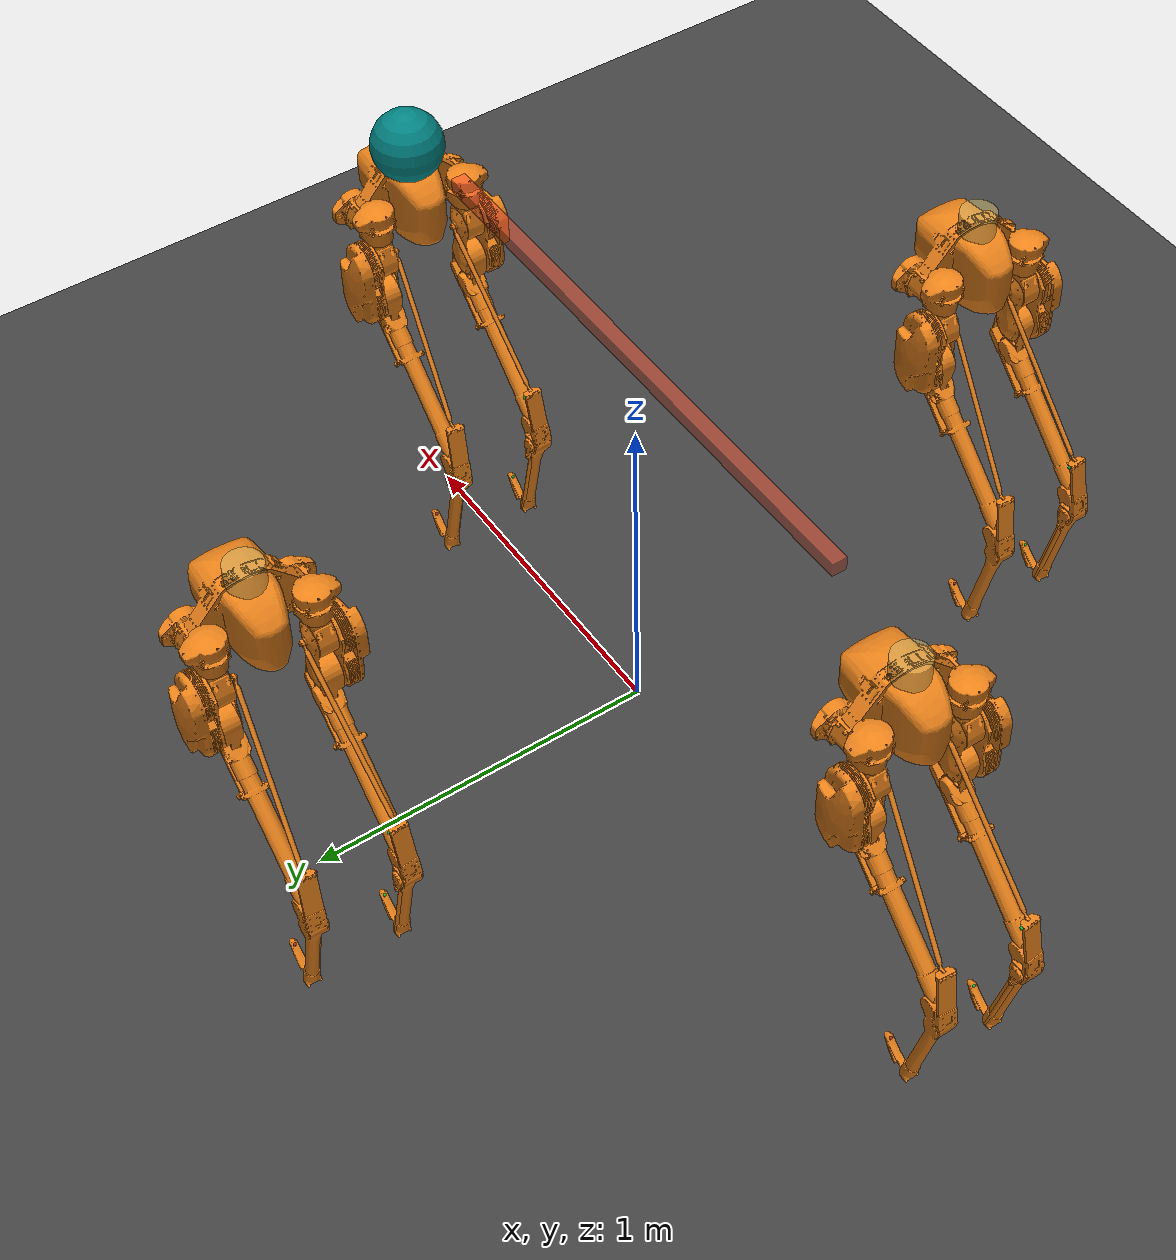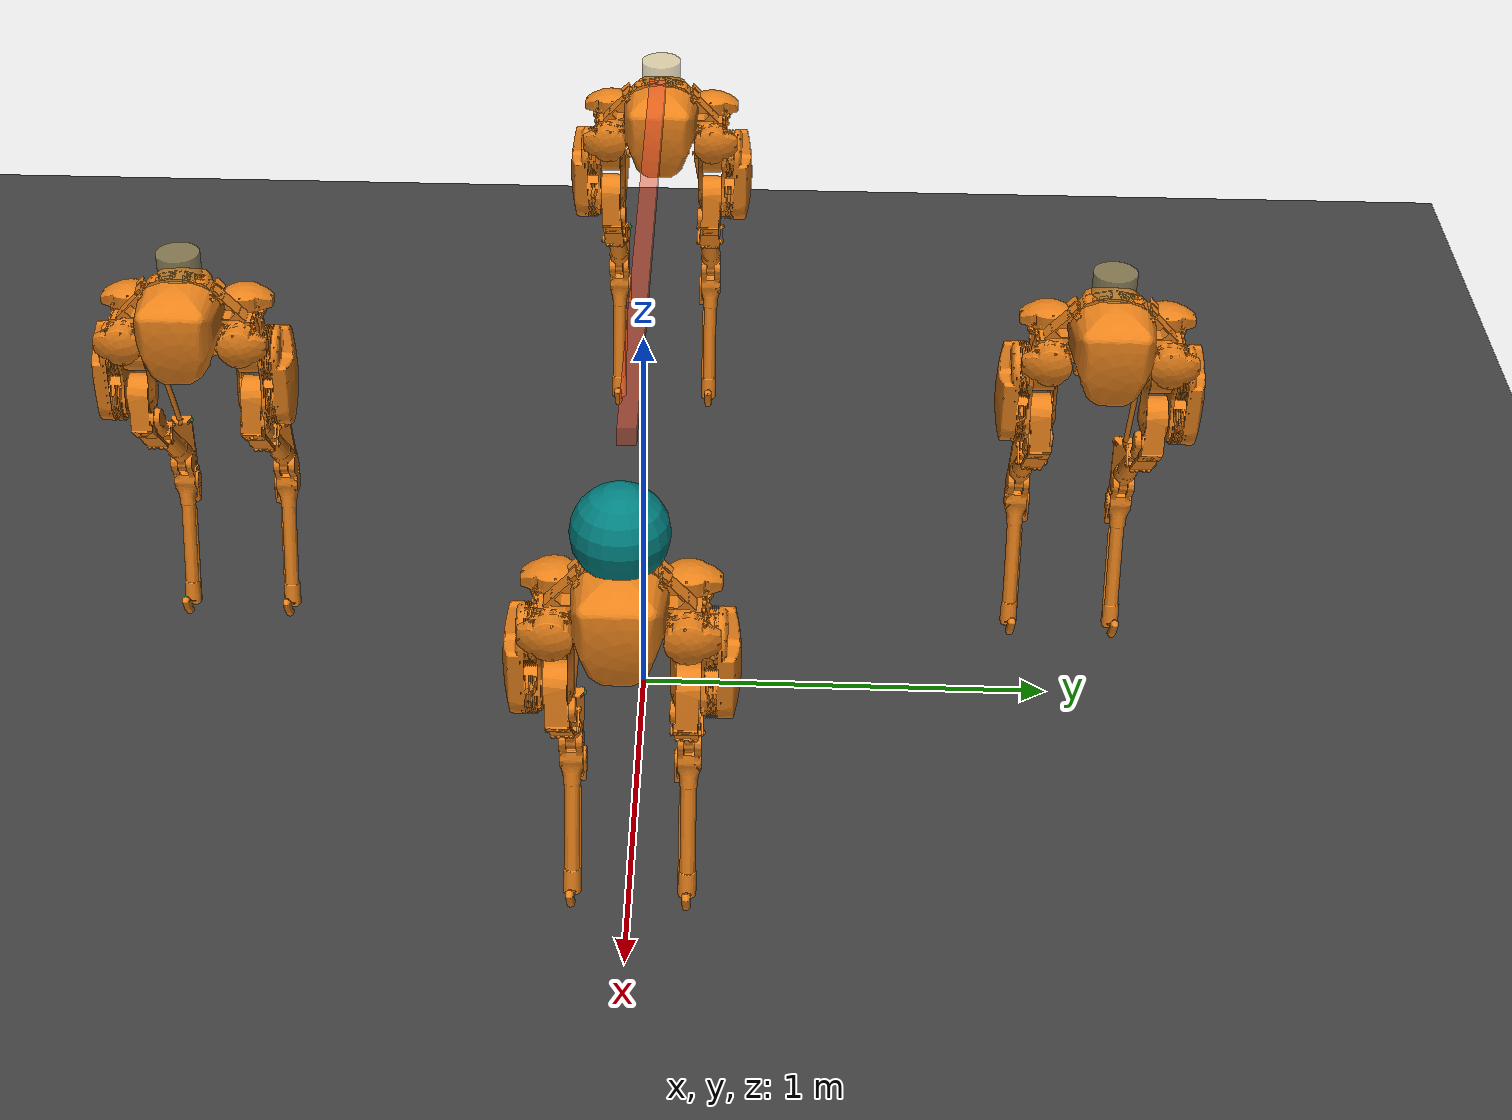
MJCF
<!-- Cassie simulation model developed by the Dynamic Robotics Laboratory -->
<mujoco model='cassie'>
  <compiler inertiafromgeom='auto' angle='degree' eulerseq='zyx' meshdir='cassie-stl-meshes'/>
  <size nuser_actuator='1' nuser_sensor='1' nuser_geom='1' nconmax='1000'/>
  <option timestep='0.0005' iterations='50' solver='Newton' gravity='0 0 -9.80665'/>
  <!-- Timestep is set to 0.0005 because our controller runs at 2 kHz -->
  <!-- Larger values still have stable dynamics -->

  <visual>
    <quality shadowsize='4096'/>
    <map znear='0.01' zfar='5'/>
    <global offwidth='848'/>
  </visual>

  <default>
    <joint limited='true'/>
    <motor ctrllimited='true'/>
    <geom contype='0' conaffinity='0' condim='1' solref='0.005 1'/>
    <equality solref='0.005 1'/>
    <default class='cassie'>
      <geom material='cassie'/>
    </default>
    <default class='collision'>
      <!-- User parameter for geoms is used to identify collision types -->
      <geom material='collision' contype='1' user='2'/>
      <default class='collision-left'>
        <geom contype='2' conaffinity='4' group='1'/>
      </default>
      <default class='collision-right'>
        <geom contype='4' conaffinity='2' group='1'/>
      </default>
    </default>
    <default class='obstacle'>
      <geom material='obstacle' condim='3' contype='8' conaffinity='15' user='1'/>
    </default>
  </default>

  <asset>
    <texture type='skybox' builtin='gradient' width='128' height='128' rgb1='0.4 0.6 0.8' rgb2='0 0 0'/>
    <texture name='plane' type='2d' builtin='checker' rgb1='0.2 0.2 0.2' rgb2='0.3 0.3 0.3' width='512' height='512'/>
    <material name='plane' reflectance='0.0' texture='plane' texrepeat='1 1' texuniform='true'/>
    <material name='cassie'    rgba='0.9 0.5 0.1 1'/>
    <material name='collision' rgba='0.1 0.5 0.9 0'/>
    <material name='obstacle'  rgba='0.2 0.6 0.2 1'/>
    <mesh name='cassie-pelvis' file='pelvis.stl'/>
    <mesh name='left-hip-roll'     file='hip-roll.stl'/>
    <mesh name='left-hip-yaw'      file='hip-yaw.stl'/>
    <mesh name='left-hip-pitch'    file='hip-pitch.stl'/>
    <mesh name='left-achilles-rod' file='achilles-rod.stl'/>
    <mesh name='left-knee'         file='knee.stl'/>
    <mesh name='left-knee-spring'  file='knee-spring.stl'/>
    <mesh name='left-shin'         file='shin.stl'/>
    <mesh name='left-tarsus'       file='tarsus.stl'/>
    <mesh name='left-heel-spring'  file='heel-spring.stl'/>
    <mesh name='left-foot-crank'   file='foot-crank.stl'/>
    <mesh name='left-plantar-rod'  file='plantar-rod.stl'/>
    <mesh name='left-foot'         file='foot.stl'/>
    <mesh name='right-hip-roll'     scale='1 -1 1' file='hip-roll.stl'/>
    <mesh name='right-hip-yaw'      scale='1 -1 1' file='hip-yaw.stl'/>
    <mesh name='right-hip-pitch'    scale='1 1 -1' file='hip-pitch.stl'/>
    <mesh name='right-achilles-rod' scale='1 1 -1' file='achilles-rod.stl'/>
    <mesh name='right-knee'         scale='1 1 -1' file='knee.stl'/>
    <mesh name='right-knee-spring'  scale='1 1 -1' file='knee-spring.stl'/>
    <mesh name='right-shin'         scale='1 1 -1' file='shin.stl'/>
    <mesh name='right-tarsus'       scale='1 1 -1' file='tarsus.stl'/>
    <mesh name='right-heel-spring'  scale='1 1 -1' file='heel-spring.stl'/>
    <mesh name='right-foot-crank'   scale='1 1 -1' file='foot-crank.stl'/>
    <mesh name='right-plantar-rod'  scale='1 1 -1' file='plantar-rod.stl'/>
    <mesh name='right-foot'         scale='1 1 -1' file='foot.stl'/>
  </asset>

  <worldbody>
    <geom name='floor' pos='0.001 0 0' size='100 100 .125' type='plane' material='plane' condim='3' conaffinity='15' priority='100'/>
    <light mode='trackcom' pos='0 0 5' dir='0 0 -1'/>
    <light directional='true' pos='0 0 3' dir='0 0 -1' diffuse='0.2 0.2 0.2' specular='0 0 0'/>

    <body name="deck" pos="0 0 1.2">

      <inertial pos='0.0 0.0 0.0' mass='0'/>

      <site name='poi_site' size='0.1' pos='1.06066017 0 0' rgba='0.0 0.5 0.5 1.0'/>

      <body name="connector_1_2" pos='0.0 0.0 0.05'>
        <geom name="connector_1_2" mass='10.0' type='box' size='0.8 0.02 0.02'
              rgba="0.93333333 0.29411765 0.16862745 0.5" class='collision' group='1'/>
      </body>

      <body name="connector_2_3" pos='0.0 0.0 0.05'>
        <geom name="connector_2_3" mass='10.0' type='box' size='0.8 0.02 0.02'
              rgba="0.93333333 0.29411765 0.16862745 0.5" class='collision' group='1'/>
      </body>

      <body name="connector_3_4" pos='0.0 0.0 0.05'>
        <geom name="connector_3_4" mass='10.0' type='box' size='0.8 0.02 0.02'
              rgba="0.93333333 0.29411765 0.16862745 0.5" class='collision' group='1'/>
      </body>

      <body name="connector_4_1" pos='0.0 0.0 0.05'>
        <geom name="connector_4_1" mass='10.0' type='box' size='0.8 0.02 0.02'
              rgba="0.93333333 0.29411765 0.16862745 0.5" class='collision' group='1'/>
      </body>

      <joint type='slide' axis='1 0 0' limited='false' name="slide_a0"/>
      <joint type='slide' axis='0 1 0' limited='false' name="slide_a1"/>
      <joint type='slide' axis='0 0 1' limited='false' name="slide_a2" ref='1.01'/>
      <joint type='ball' limited='false'/>

      <body name='cassie-pelvis' pos='1.06066017 0 -0.2' childclass='cassie'>
          <geom type="cylinder" size="0.05 0.05" pos="0 0 0.15" rgba="0.8 0.7 0.4 0.5"/>
          <camera name='track' pos='0 -3 1' zaxis='0 -1 0.5' mode='track'/>
          <site name='cassie-pelvis_site' size='0.01' pos='0.0 0.0 0.0' rgba='0.0 0.0 0.5 1.0'/>
          <camera name='realsense-d455' pos='.1856 0 0.24' euler='-90 0 30' fovy='58'/>
          <inertial pos='0.05066 0.000346 0.02841' mass='10.33' fullinertia='0.085821 0.049222 0.08626 1.276e-05 -0.00016022 -0.000414'/>

          <joint type='hinge' axis="1 0 0" limited='false'/>
          <joint type='hinge' axis="0 1 0" limited='false'/>
          <joint type='hinge' axis="0 0 1" limited='false'/>

          <geom type='mesh' mesh='cassie-pelvis'/>
          <geom type='sphere' size='0.15' pos='0.02 0 0.02' class='collision' group='1'/>
          <site name='imu' size='0.01' pos='0.03155 0 -0.07996' rgba='0.5 0.5 0.5 1.0'/>
          <body name='left-hip-roll' pos='0.021 0.135 0' xyaxes='0 0 -1 0 1 0'>
            <inertial pos='-0.01793 0.0001 -0.04428' mass='1.82' fullinertia='0.003431 0.003793 0.002135 -6.65e-07 -0.00084 3.99e-06'/>
            <joint name='left-hip-roll' type='hinge' range='-15 22.5' damping='1' armature='0.038125'/>
            <geom type='mesh' mesh='left-hip-roll'/>
            <body name='left-hip-yaw' pos='0 0 -0.07' xyaxes='0 0 1 0 1 0'>
              <inertial pos='0 -1e-05 -0.034277' mass='1.171' fullinertia='0.002443 0.002803 0.000842 -4e-08 2.462e-07 -2.71e-08'/>
              <joint name='left-hip-yaw' type='hinge' range='-22.5 22.5' damping='1' armature='0.038125'/>
              <geom type='mesh' mesh='left-hip-yaw'/>
              <body name='left-hip-pitch' pos='0 0 -0.09' xyaxes='0 0 -1 1 0 0'>
                <inertial pos='0.05946 5e-05 -0.03581' mass='5.52' fullinertia='0.010898 0.029714 0.030257 -0.0002669 -5.721e-05 9.17e-06'/>
                <joint name='left-hip-pitch' type='hinge' range='-50 80' damping='1' armature='0.09344'/>
                <geom type='mesh' mesh='left-hip-pitch'/>
                <geom type='capsule' size='0.08' fromto='0 0 -0.04 0.12 0 -0.0355' class='collision' group='1'/>
                <body name='left-achilles-rod' pos='0 0 0.045' xyaxes='0.7922 -0.60599 -0.072096 0.60349 0.79547 -0.054922'>
                  <inertial pos='0.24719 0 0' mass='0.1567' fullinertia='3.754e-06 0.004487 0.004488 -3.74e-08 -1.61e-08 0'/>
                  <joint name='left-achilles-rod' type='ball' limited='false' damping='0.01'/>
                  <geom type='mesh' mesh='left-achilles-rod'/>
                  <geom type='capsule' size='0.008' fromto='0 0 0 0.5012 0.0 0' class='collision-left'/>
                </body>
                <body name='left-knee' pos='0.12 0 0.0045' xyaxes='0.70711 -0.70711 0 0.70711 0.70711 0'>
                  <inertial pos='0.023 0.03207 -0.002181' mass='0.7578' fullinertia='0.001376 0.0010335 0.0021637 -0.00039744 -4.085e-05 -5.374e-05'/>
                  <joint name='left-knee' type='hinge' ref='-45' range='-164 -37' damping='1' armature='0.09344'/>
                  <geom type='mesh' mesh='left-knee'/>
                  <body name='left-knee-spring' pos='0.06068 0.08241 0'>
                    <inertial pos='0.0836 0.0034 0' mass='0.186' fullinertia='5.215e-05 0.00041205 0.0003669 6.87e-06 0 0'/>
                    <geom type='mesh' mesh='left-knee-spring'/>
                  </body>
                  <body name='left-shin' pos='0.06068 0.04741 0'>
                    <inertial pos='0.18338 0.001169 0.0002123' mass='0.577' fullinertia='0.00035939 0.014728 0.014707 -0.00020981 2.266e-05 -1.2e-07'/>
                    <joint name='left-shin' type='hinge' range='-20 20' stiffness='1500' damping='0.1'/>
                    <geom type='mesh' mesh='left-shin'/>
                    <geom type='capsule' size='0.04' fromto='0 0 0 0.43476 0.02 0' class='collision-left'/>
                    <body name='left-tarsus' pos='0.43476 0.02 0' xyaxes='0.52992 0.84805 0 -0.84805 0.52992 0'>
                      <inertial pos='0.11046 -0.03058 -0.00131' mass='0.782' fullinertia='0.00039238 0.013595 0.013674 0.00023651 -4.987e-05 -4.82e-06'/>
                      <joint name='left-tarsus' type='hinge' ref='58' range='50 170' damping='0.1'/>
                      <geom type='mesh' mesh='left-tarsus'/>
                      <geom type='capsule' size='0.04' fromto='-0.01269 -0.03059 0.00092 0.408 -0.04 0' class='collision-left'/>
                      <body name='left-heel-spring' pos='-0.01269 -0.03059 0.00092' xyaxes='-0.91211 0.40829 0.036948 -0.40992 -0.90952 -0.068841'>
                        <inertial pos='0.081 0.0022 0' mass='0.126' fullinertia='2.959e-05 0.00022231 0.0002007 7.15e-06 -6e-07 1e-07'/>
                        <joint name='left-heel-spring' type='hinge' limited='false' stiffness='1250'/>
                        <geom type='mesh' mesh='left-heel-spring'/>
                        <geom type='box' size='0.09 0.005 0.04' pos='0.035 0.005 0.0' class='collision-left'/>
                        <site name="left-heel-spring-pt" type="sphere" pos="0.11877 0.0 0.025" size="0.005" rgba="0.7 0.2 0.1 1.0"/>
                      </body>
                      <body name='left-foot-crank' pos='0.058 -0.034 0.02275'>
                        <inertial pos='0.00493 2e-05 -0.00215' mass='0.1261' fullinertia='2.6941e-05 4.9621e-05 6.3362e-05 -2.1e-09 -3.9623e-06 -1.09e-08'/>
                        <joint name='left-foot-crank' type='hinge' range='-140 -30' damping='1'/>
                        <geom type='mesh' mesh='left-foot-crank' contype='2' conaffinity='4'/>
                        <body name='left-plantar-rod' pos='0.055 0 -0.00791'>
                          <inertial pos='0.17792 0 0' mass='0.1186' fullinertia='2.779e-06 0.001774 0.001775 -2.34e-08 -8.1e-09 0'/>
                          <joint name='left-plantar-rod' type='hinge' limited='false' damping='0.01'/>
                          <geom type='mesh' mesh='left-plantar-rod'/>
                          <geom type='capsule' size='0.008' fromto='0 0 0 0.35012 0.0 0' class='collision-left'/>
                          <site name="left-plantar-rod-pt" type="sphere" pos="0.17506 0.0 0.0" size="0.005" rgba="0.7 0.2 0.1 1.0"/>
                        </body>
                      </body>
                      <body name='left-foot' pos='0.408 -0.04 0'>
                        <inertial pos='0.00474 0.02748 -0.00014' mass='0.1498' fullinertia='0.00017388 0.00016793 0.00033261 0.00011814 1.36e-06 -4e-07'/>
                        <joint name='left-foot' type='hinge' range='-140 -30' damping='1' armature='0.01225'/>
                        <geom type='mesh' mesh='left-foot'/>
                        <geom type='capsule' size='0.02' fromto='-0.052821 0.092622 0 0.069746 -0.010224 0' class='collision-left'/>
                        <site name="left-foot-mid" type="sphere" pos="0.01762 0.05219 0" euler="140 0 -90" size="0.005" rgba="0.7 0.2 0.1 1.0"/>
                        <site name="left-toe" type="sphere" pos="-0.052821 0.092622 0" size="0.005" rgba="0.7 0.2 0.1 1.0"/>
                        <site name="left-heel" type="sphere" pos="0.069746 -0.010224 0" size="0.005" rgba="0.7 0.2 0.1 1.0"/>
                      </body>
                    </body>
                  </body>
                </body>
              </body>
            </body>
          </body>
          <body name='right-hip-roll' pos='0.021 -0.135 0' xyaxes='0 0 -1 0 1 0'>
             <inertial pos='-0.01793 0.0001 -0.04428' mass='1.82' fullinertia='0.003431 0.003793 0.002135 6.65e-07 -0.00084 -3.99e-06'/>
            <joint name='right-hip-roll' type='hinge' range='-22.5 15' damping='1' armature='0.038125'/>
            <geom type='mesh' mesh='right-hip-roll'/>
            <body name='right-hip-yaw' pos='0 0 -0.07' xyaxes='0 0 1 0 1 0'>
              <inertial pos='0 1e-05 -0.034277' mass='1.171' fullinertia='0.002443 0.002803 0.000842 4e-08 2.462e-07 2.71e-08'/>
              <joint name='right-hip-yaw' type='hinge' range='-22.5 22.5' damping='1' armature='0.038125'/>
              <geom type='mesh' mesh='right-hip-yaw'/>
              <body name='right-hip-pitch' pos='0 0 -0.09' xyaxes='0 0 -1 1 0 0'>
                <inertial pos='0.05946 5e-05 0.03581' mass='5.52' fullinertia='0.010898 0.029714 0.030257 -0.0002669 5.721e-05 -9.17e-06'/>
                <joint name='right-hip-pitch' type='hinge' range='-50 80' damping='1' armature='0.09344'/>
                <geom type='mesh' mesh='right-hip-pitch'/>
                <geom type='capsule' size='0.08' fromto='0 0 0.04 0.12 0 0.0355' class='collision' group='1'/>
                <body name='right-achilles-rod' pos='0 0 -0.045' xyaxes='0.7922 -0.60599 0.072096 0.60349 0.79547 0.054922'>
                  <inertial pos='0.24719 0 0' mass='0.1567' fullinertia='3.754e-06 0.004487 0.004488 -3.74e-08 1.61e-08 0'/>
                  <joint name='right-achilles-rod' type='ball' limited='false' damping='0.01'/>
                  <geom type='mesh' mesh='right-achilles-rod'/>
                  <geom type='capsule' size='0.008' fromto='0 0 0 0.5012 0.0 0' class='collision-right'/>
                </body>
                <body name='right-knee' pos='0.12 0 -0.0045' xyaxes='0.70711 -0.70711 0 0.70711 0.70711 0'>
                  <inertial pos='0.023 0.03207 0.002181' mass='0.7578' fullinertia='0.001376 0.0010335 0.0021637 -0.00039744 4.085e-05 5.374e-05'/>
                  <joint name='right-knee' type='hinge' ref='-45' range='-164 -37' damping='1' armature='0.09344'/>
                  <geom type='mesh' mesh='right-knee'/>
                  <body name='right-knee-spring' pos='0.06068 0.08241 0'>
                    <inertial pos='0.0836 0.0034 0' mass='0.186' fullinertia='5.215e-05 0.00041205 0.0003669 6.87e-06 0 0'/>
                    <geom type='mesh' mesh='right-knee-spring'/>
                  </body>
                  <body name='right-shin' pos='0.06068 0.04741 0'>
                    <inertial pos='0.18338 0.001169 -0.0002123' mass='0.577' fullinertia='0.00035939 0.014728 0.014707 -0.00020981 -2.266e-05 1.2e-07'/>
                    <joint name='right-shin' type='hinge' range='-20 20' stiffness='1500' damping='0.1'/>
                    <geom type='mesh' mesh='right-shin'/>
                    <geom type='capsule' size='0.04' fromto='0 0 0 0.43476 0.02 0' class='collision-right'/>
                    <body name='right-tarsus' pos='0.43476 0.02 0' xyaxes='0.52992 0.84805 0 -0.84805 0.52992 0'>
                      <inertial pos='0.11046 -0.03058 0.00131' mass='0.782' fullinertia='0.00039238 0.013595 0.013674 0.00023651 4.987e-05 4.82e-06'/>
                      <joint name='right-tarsus' type='hinge' ref='58' range='50 170' damping='0.1'/>
                      <geom type='mesh' mesh='right-tarsus'/>
                      <geom type='capsule' size='0.04' fromto='-0.01269 -0.03059 -0.00092 0.408 -0.04 0' class='collision-right'/>
                      <body name='right-heel-spring' pos='-0.01269 -0.03059 -0.00092' xyaxes='-0.91211 0.40829 -0.036948 -0.40992 -0.90952 0.068841'>
                        <inertial pos='0.081 0.0022 0' mass='0.126' fullinertia='2.959e-05 0.00022231 0.0002007 7.15e-06 6e-07 -1e-07'/>
                        <joint name='right-heel-spring' type='hinge' limited='false' stiffness='1250'/>
                        <geom type='mesh' mesh='right-heel-spring'/>
                        <geom type='box' size='0.09 0.005 0.04' pos='0.035 0.005 0.0' class='collision-right'/>
                        <site name="right-heel-spring-pt" type="sphere" pos="0.11877 0.0 -0.025" size="0.005" rgba="0.1 0.7 0.2 1.0"/>
                      </body>
                      <body name='right-foot-crank' pos='0.058 -0.034 -0.02275'>
                        <inertial pos='0.00493 2e-05 0.00215' mass='0.1261' fullinertia='2.6941e-05 4.9621e-05 6.3362e-05 -2.1e-09 3.9623e-06 1.09e-08'/>
                        <joint name='right-foot-crank' type='hinge' range='-140 -30' damping='1'/>
                        <geom type='mesh' mesh='right-foot-crank' contype='4' conaffinity='2'/>
                        <body name='right-plantar-rod' pos='0.055 0 0.00791'>
                          <inertial pos='0.17792 0 0' mass='0.1186' fullinertia='2.779e-06 0.001774 0.001775 -2.34e-08 8.1e-09 0'/>
                          <joint name='right-plantar-rod' type='hinge' limited='false' damping='0.01'/>
                          <geom type='mesh' mesh='right-plantar-rod'/>
                          <geom type='capsule' size='0.008' fromto='0 0 0 0.35012 0.0 0' class='collision-right'/>
                          <site name="right-plantar-rod-pt" type="sphere" pos="0.17506 0.0 0.0" size="0.005" rgba="0.1 0.7 0.2 1.0"/>
                        </body>
                      </body>
                      <body name='right-foot' pos='0.408 -0.04 0'>
                        <inertial pos='0.00474 0.02748 0.00014' mass='0.1498' fullinertia='0.00017388 0.00016793 0.00033261 0.00011814 -1.36e-06 4e-07'/>
                        <joint name='right-foot' type='hinge' range='-140 -30' damping='1' armature='0.01225'/>
                        <geom type='mesh' mesh='right-foot'/>
                        <geom type='capsule' size='0.02' fromto='-0.052821 0.092622 0 0.069746 -0.010224 0' class='collision-right'/>
                        <site name="right-foot-mid" type="sphere" pos="0.01762 0.05219 0" euler="140 0 -90" size="0.005" rgba="0.7 0.2 0.1 1.0"/>
                        <site name="right-toe" type="sphere" pos="-0.052821 0.092622 0.0" size="0.005" rgba="0.1 0.7 0.2 1.0"/>
                        <site name="right-heel" type="sphere" pos="0.069746 -0.010224 0" size="0.005" rgba="0.1 0.7 0.2 1.0"/>
                      </body>
                    </body>
                  </body>
                </body>
              </body>
            </body>
          </body>
        </body>

      <body name='c2_cassie-pelvis' pos='0 1.06066017 -0.2' childclass='cassie'>
        <geom type="cylinder" size="0.05 0.05" pos="0 0 0.15" rgba="0.8 0.7 0.4 0.5"/>
        <site name='c2_cassie-pelvis_site' size='0.01' pos='0.0 0.0 0.0' rgba='0.0 0.0 0.5 1.0'/>
        <camera name='c2_track' pos='0 -3 1' zaxis='0 -1 0.5' mode='track'/>
        <camera name='c2_realsense-d455' pos='.1856 0 0.24' euler='-90 0 30' fovy='58'/>
        <inertial pos='0.05066 0.000346 0.02841' mass='10.33' fullinertia='0.085821 0.049222 0.08626 1.276e-05 -0.00016022 -0.000414'/>

        <joint type='hinge' axis="1 0 0" limited='false'/>
        <joint type='hinge' axis="0 1 0" limited='false'/>
        <joint type='hinge' axis="0 0 1" limited='false'/>

        <geom type='mesh' mesh='cassie-pelvis'/>
        <geom type='sphere' size='0.15' pos='0.02 0 0.02' class='collision' group='1'/>
        <site name='c2_imu' size='0.01' pos='0.03155 0 -0.07996' rgba='0.5 0.5 0.5 1.0'/>
        <body name='c2_left-hip-roll' pos='0.021 0.135 0' xyaxes='0 0 -1 0 1 0'>
          <inertial pos='-0.01793 0.0001 -0.04428' mass='1.82' fullinertia='0.003431 0.003793 0.002135 -6.65e-07 -0.00084 3.99e-06'/>
          <joint name='c2_left-hip-roll' type='hinge' range='-15 22.5' damping='1' armature='0.038125'/>
          <geom type='mesh' mesh='left-hip-roll'/>
          <body name='c2_left-hip-yaw' pos='0 0 -0.07' xyaxes='0 0 1 0 1 0'>
            <inertial pos='0 -1e-05 -0.034277' mass='1.171' fullinertia='0.002443 0.002803 0.000842 -4e-08 2.462e-07 -2.71e-08'/>
            <joint name='c2_left-hip-yaw' type='hinge' range='-22.5 22.5' damping='1' armature='0.038125'/>
            <geom type='mesh' mesh='left-hip-yaw'/>
            <body name='c2_left-hip-pitch' pos='0 0 -0.09' xyaxes='0 0 -1 1 0 0'>
              <inertial pos='0.05946 5e-05 -0.03581' mass='5.52' fullinertia='0.010898 0.029714 0.030257 -0.0002669 -5.721e-05 9.17e-06'/>
              <joint name='c2_left-hip-pitch' type='hinge' range='-50 80' damping='1' armature='0.09344'/>
              <geom type='mesh' mesh='left-hip-pitch'/>
              <geom type='capsule' size='0.08' fromto='0 0 -0.04 0.12 0 -0.0355' class='collision' group='1'/>
              <body name='c2_left-achilles-rod' pos='0 0 0.045' xyaxes='0.7922 -0.60599 -0.072096 0.60349 0.79547 -0.054922'>
                <inertial pos='0.24719 0 0' mass='0.1567' fullinertia='3.754e-06 0.004487 0.004488 -3.74e-08 -1.61e-08 0'/>
                <joint name='c2_left-achilles-rod' type='ball' limited='false' damping='0.01'/>
                <geom type='mesh' mesh='left-achilles-rod'/>
                <geom type='capsule' size='0.008' fromto='0 0 0 0.5012 0.0 0' class='collision-left'/>
              </body>
              <body name='c2_left-knee' pos='0.12 0 0.0045' xyaxes='0.70711 -0.70711 0 0.70711 0.70711 0'>
                <inertial pos='0.023 0.03207 -0.002181' mass='0.7578' fullinertia='0.001376 0.0010335 0.0021637 -0.00039744 -4.085e-05 -5.374e-05'/>
                <joint name='c2_left-knee' type='hinge' ref='-45' range='-164 -37' damping='1' armature='0.09344'/>
                <geom type='mesh' mesh='left-knee'/>
                <body name='c2_left-knee-spring' pos='0.06068 0.08241 0'>
                  <inertial pos='0.0836 0.0034 0' mass='0.186' fullinertia='5.215e-05 0.00041205 0.0003669 6.87e-06 0 0'/>
                  <geom type='mesh' mesh='left-knee-spring'/>
                </body>
                <body name='c2_left-shin' pos='0.06068 0.04741 0'>
                  <inertial pos='0.18338 0.001169 0.0002123' mass='0.577' fullinertia='0.00035939 0.014728 0.014707 -0.00020981 2.266e-05 -1.2e-07'/>
                  <joint name='c2_left-shin' type='hinge' range='-20 20' stiffness='1500' damping='0.1'/>
                  <geom type='mesh' mesh='left-shin'/>
                  <geom type='capsule' size='0.04' fromto='0 0 0 0.43476 0.02 0' class='collision-left'/>
                  <body name='c2_left-tarsus' pos='0.43476 0.02 0' xyaxes='0.52992 0.84805 0 -0.84805 0.52992 0'>
                    <inertial pos='0.11046 -0.03058 -0.00131' mass='0.782' fullinertia='0.00039238 0.013595 0.013674 0.00023651 -4.987e-05 -4.82e-06'/>
                    <joint name='c2_left-tarsus' type='hinge' ref='58' range='50 170' damping='0.1'/>
                    <geom type='mesh' mesh='left-tarsus'/>
                    <geom type='capsule' size='0.04' fromto='-0.01269 -0.03059 0.00092 0.408 -0.04 0' class='collision-left'/>
                    <body name='c2_left-heel-spring' pos='-0.01269 -0.03059 0.00092' xyaxes='-0.91211 0.40829 0.036948 -0.40992 -0.90952 -0.068841'>
                      <inertial pos='0.081 0.0022 0' mass='0.126' fullinertia='2.959e-05 0.00022231 0.0002007 7.15e-06 -6e-07 1e-07'/>
                      <joint name='c2_left-heel-spring' type='hinge' limited='false' stiffness='1250'/>
                      <geom type='mesh' mesh='left-heel-spring'/>
                      <geom type='box' size='0.09 0.005 0.04' pos='0.035 0.005 0.0' class='collision-left'/>
                      <site name="c2_left-heel-spring-pt" type="sphere" pos="0.11877 0.0 0.025" size="0.005" rgba="0.7 0.2 0.1 1.0"/>
                    </body>
                    <body name='c2_left-foot-crank' pos='0.058 -0.034 0.02275'>
                      <inertial pos='0.00493 2e-05 -0.00215' mass='0.1261' fullinertia='2.6941e-05 4.9621e-05 6.3362e-05 -2.1e-09 -3.9623e-06 -1.09e-08'/>
                      <joint name='c2_left-foot-crank' type='hinge' range='-140 -30' damping='1'/>
                      <geom type='mesh' mesh='left-foot-crank' contype='2' conaffinity='4'/>
                      <body name='c2_left-plantar-rod' pos='0.055 0 -0.00791'>
                        <inertial pos='0.17792 0 0' mass='0.1186' fullinertia='2.779e-06 0.001774 0.001775 -2.34e-08 -8.1e-09 0'/>
                        <joint name='c2_left-plantar-rod' type='hinge' limited='false' damping='0.01'/>
                        <geom type='mesh' mesh='left-plantar-rod'/>
                        <geom type='capsule' size='0.008' fromto='0 0 0 0.35012 0.0 0' class='collision-left'/>
                        <site name="c2_left-plantar-rod-pt" type="sphere" pos="0.17506 0.0 0.0" size="0.005" rgba="0.7 0.2 0.1 1.0"/>
                      </body>
                    </body>
                    <body name='c2_left-foot' pos='0.408 -0.04 0'>
                      <inertial pos='0.00474 0.02748 -0.00014' mass='0.1498' fullinertia='0.00017388 0.00016793 0.00033261 0.00011814 1.36e-06 -4e-07'/>
                      <joint name='c2_left-foot' type='hinge' range='-140 -30' damping='1' armature='0.01225'/>
                      <geom type='mesh' mesh='left-foot'/>
                      <geom type='capsule' size='0.02' fromto='-0.052821 0.092622 0 0.069746 -0.010224 0' class='collision-left'/>
                      <site name="c2_left-foot-mid" type="sphere" pos="0.01762 0.05219 0" euler="140 0 -90" size="0.005" rgba="0.7 0.2 0.1 1.0"/>
                      <site name="c2_left-toe" type="sphere" pos="-0.052821 0.092622 0" size="0.005" rgba="0.7 0.2 0.1 1.0"/>
                      <site name="c2_left-heel" type="sphere" pos="0.069746 -0.010224 0" size="0.005" rgba="0.7 0.2 0.1 1.0"/>
                    </body>
                  </body>
                </body>
              </body>
            </body>
          </body>
        </body>
        <body name='c2_right-hip-roll' pos='0.021 -0.135 0' xyaxes='0 0 -1 0 1 0'>
          <inertial pos='-0.01793 0.0001 -0.04428' mass='1.82' fullinertia='0.003431 0.003793 0.002135 6.65e-07 -0.00084 -3.99e-06'/>
          <joint name='c2_right-hip-roll' type='hinge' range='-22.5 15' damping='1' armature='0.038125'/>
          <geom type='mesh' mesh='right-hip-roll'/>
          <body name='c2_right-hip-yaw' pos='0 0 -0.07' xyaxes='0 0 1 0 1 0'>
            <inertial pos='0 1e-05 -0.034277' mass='1.171' fullinertia='0.002443 0.002803 0.000842 4e-08 2.462e-07 2.71e-08'/>
            <joint name='c2_right-hip-yaw' type='hinge' range='-22.5 22.5' damping='1' armature='0.038125'/>
            <geom type='mesh' mesh='right-hip-yaw'/>
            <body name='c2_right-hip-pitch' pos='0 0 -0.09' xyaxes='0 0 -1 1 0 0'>
              <inertial pos='0.05946 5e-05 0.03581' mass='5.52' fullinertia='0.010898 0.029714 0.030257 -0.0002669 5.721e-05 -9.17e-06'/>
              <joint name='c2_right-hip-pitch' type='hinge' range='-50 80' damping='1' armature='0.09344'/>
              <geom type='mesh' mesh='right-hip-pitch'/>
              <geom type='capsule' size='0.08' fromto='0 0 0.04 0.12 0 0.0355' class='collision' group='1'/>
              <body name='c2_right-achilles-rod' pos='0 0 -0.045' xyaxes='0.7922 -0.60599 0.072096 0.60349 0.79547 0.054922'>
                <inertial pos='0.24719 0 0' mass='0.1567' fullinertia='3.754e-06 0.004487 0.004488 -3.74e-08 1.61e-08 0'/>
                <joint name='c2_right-achilles-rod' type='ball' limited='false' damping='0.01'/>
                <geom type='mesh' mesh='right-achilles-rod'/>
                <geom type='capsule' size='0.008' fromto='0 0 0 0.5012 0.0 0' class='collision-right'/>
              </body>
              <body name='c2_right-knee' pos='0.12 0 -0.0045' xyaxes='0.70711 -0.70711 0 0.70711 0.70711 0'>
                <inertial pos='0.023 0.03207 0.002181' mass='0.7578' fullinertia='0.001376 0.0010335 0.0021637 -0.00039744 4.085e-05 5.374e-05'/>
                <joint name='c2_right-knee' type='hinge' ref='-45' range='-164 -37' damping='1' armature='0.09344'/>
                <geom type='mesh' mesh='right-knee'/>
                <body name='c2_right-knee-spring' pos='0.06068 0.08241 0'>
                  <inertial pos='0.0836 0.0034 0' mass='0.186' fullinertia='5.215e-05 0.00041205 0.0003669 6.87e-06 0 0'/>
                  <geom type='mesh' mesh='right-knee-spring'/>
                </body>
                <body name='c2_right-shin' pos='0.06068 0.04741 0'>
                  <inertial pos='0.18338 0.001169 -0.0002123' mass='0.577' fullinertia='0.00035939 0.014728 0.014707 -0.00020981 -2.266e-05 1.2e-07'/>
                  <joint name='c2_right-shin' type='hinge' range='-20 20' stiffness='1500' damping='0.1'/>
                  <geom type='mesh' mesh='right-shin'/>
                  <geom type='capsule' size='0.04' fromto='0 0 0 0.43476 0.02 0' class='collision-right'/>
                  <body name='c2_right-tarsus' pos='0.43476 0.02 0' xyaxes='0.52992 0.84805 0 -0.84805 0.52992 0'>
                    <inertial pos='0.11046 -0.03058 0.00131' mass='0.782' fullinertia='0.00039238 0.013595 0.013674 0.00023651 4.987e-05 4.82e-06'/>
                    <joint name='c2_right-tarsus' type='hinge' ref='58' range='50 170' damping='0.1'/>
                    <geom type='mesh' mesh='right-tarsus'/>
                    <geom type='capsule' size='0.04' fromto='-0.01269 -0.03059 -0.00092 0.408 -0.04 0' class='collision-right'/>
                    <body name='c2_right-heel-spring' pos='-0.01269 -0.03059 -0.00092' xyaxes='-0.91211 0.40829 -0.036948 -0.40992 -0.90952 0.068841'>
                      <inertial pos='0.081 0.0022 0' mass='0.126' fullinertia='2.959e-05 0.00022231 0.0002007 7.15e-06 6e-07 -1e-07'/>
                      <joint name='c2_right-heel-spring' type='hinge' limited='false' stiffness='1250'/>
                      <geom type='mesh' mesh='right-heel-spring'/>
                      <geom type='box' size='0.09 0.005 0.04' pos='0.035 0.005 0.0' class='collision-right'/>
                      <site name="c2_right-heel-spring-pt" type="sphere" pos="0.11877 0.0 -0.025" size="0.005" rgba="0.1 0.7 0.2 1.0"/>
                    </body>
                    <body name='c2_right-foot-crank' pos='0.058 -0.034 -0.02275'>
                      <inertial pos='0.00493 2e-05 0.00215' mass='0.1261' fullinertia='2.6941e-05 4.9621e-05 6.3362e-05 -2.1e-09 3.9623e-06 1.09e-08'/>
                      <joint name='c2_right-foot-crank' type='hinge' range='-140 -30' damping='1'/>
                      <geom type='mesh' mesh='right-foot-crank' contype='4' conaffinity='2'/>
                      <body name='c2_right-plantar-rod' pos='0.055 0 0.00791'>
                        <inertial pos='0.17792 0 0' mass='0.1186' fullinertia='2.779e-06 0.001774 0.001775 -2.34e-08 8.1e-09 0'/>
                        <joint name='c2_right-plantar-rod' type='hinge' limited='false' damping='0.01'/>
                        <geom type='mesh' mesh='right-plantar-rod'/>
                        <geom type='capsule' size='0.008' fromto='0 0 0 0.35012 0.0 0' class='collision-right'/>
                        <site name="c2_right-plantar-rod-pt" type="sphere" pos="0.17506 0.0 0.0" size="0.005" rgba="0.1 0.7 0.2 1.0"/>
                      </body>
                    </body>
                    <body name='c2_right-foot' pos='0.408 -0.04 0'>
                      <inertial pos='0.00474 0.02748 0.00014' mass='0.1498' fullinertia='0.00017388 0.00016793 0.00033261 0.00011814 -1.36e-06 4e-07'/>
                      <joint name='c2_right-foot' type='hinge' range='-140 -30' damping='1' armature='0.01225'/>
                      <geom type='mesh' mesh='right-foot'/>
                      <geom type='capsule' size='0.02' fromto='-0.052821 0.092622 0 0.069746 -0.010224 0' class='collision-right'/>
                      <site name="c2_right-foot-mid" type="sphere" pos="0.01762 0.05219 0" euler="140 0 -90" size="0.005" rgba="0.7 0.2 0.1 1.0"/>
                      <site name="c2_right-toe" type="sphere" pos="-0.052821 0.092622 0.0" size="0.005" rgba="0.1 0.7 0.2 1.0"/>
                      <site name="c2_right-heel" type="sphere" pos="0.069746 -0.010224 0" size="0.005" rgba="0.1 0.7 0.2 1.0"/>
                    </body>
                  </body>
                </body>
              </body>
            </body>
          </body>
        </body>
      </body>

      <body name='c3_cassie-pelvis' pos='-1.06066017 0 -0.2' childclass='cassie'>
        <geom type="cylinder" size="0.05 0.05" pos="0 0 0.15" rgba="0.8 0.7 0.4 0.5"/>
        <site name='c3_cassie-pelvis_site' size='0.01' pos='0.0 0.0 0.0' rgba='0.0 0.0 0.5 1.0'/>
        <camera name='c3_track' pos='0 -3 1' zaxis='0 -1 0.5' mode='track'/>
        <camera name='c3_realsense-d455' pos='.1856 0 0.24' euler='-90 0 30' fovy='58'/>
        <inertial pos='0.05066 0.000346 0.02841' mass='10.33' fullinertia='0.085821 0.049222 0.08626 1.276e-05 -0.00016022 -0.000414'/>

        <joint type='hinge' axis="1 0 0" limited='false'/>
        <joint type='hinge' axis="0 1 0" limited='false'/>
        <joint type='hinge' axis="0 0 1" limited='false'/>

        <geom type='mesh' mesh='cassie-pelvis'/>
        <geom type='sphere' size='0.15' pos='0.02 0 0.02' class='collision' group='1'/>
        <site name='c3_imu' size='0.01' pos='0.03155 0 -0.07996' rgba='0.5 0.5 0.5 1.0'/>
        <body name='c3_left-hip-roll' pos='0.021 0.135 0' xyaxes='0 0 -1 0 1 0'>
          <inertial pos='-0.01793 0.0001 -0.04428' mass='1.82' fullinertia='0.003431 0.003793 0.002135 -6.65e-07 -0.00084 3.99e-06'/>
          <joint name='c3_left-hip-roll' type='hinge' range='-15 22.5' damping='1' armature='0.038125'/>
          <geom type='mesh' mesh='left-hip-roll'/>
          <body name='c3_left-hip-yaw' pos='0 0 -0.07' xyaxes='0 0 1 0 1 0'>
            <inertial pos='0 -1e-05 -0.034277' mass='1.171' fullinertia='0.002443 0.002803 0.000842 -4e-08 2.462e-07 -2.71e-08'/>
            <joint name='c3_left-hip-yaw' type='hinge' range='-22.5 22.5' damping='1' armature='0.038125'/>
            <geom type='mesh' mesh='left-hip-yaw'/>
            <body name='c3_left-hip-pitch' pos='0 0 -0.09' xyaxes='0 0 -1 1 0 0'>
              <inertial pos='0.05946 5e-05 -0.03581' mass='5.52' fullinertia='0.010898 0.029714 0.030257 -0.0002669 -5.721e-05 9.17e-06'/>
              <joint name='c3_left-hip-pitch' type='hinge' range='-50 80' damping='1' armature='0.09344'/>
              <geom type='mesh' mesh='left-hip-pitch'/>
              <geom type='capsule' size='0.08' fromto='0 0 -0.04 0.12 0 -0.0355' class='collision' group='1'/>
              <body name='c3_left-achilles-rod' pos='0 0 0.045' xyaxes='0.7922 -0.60599 -0.072096 0.60349 0.79547 -0.054922'>
                <inertial pos='0.24719 0 0' mass='0.1567' fullinertia='3.754e-06 0.004487 0.004488 -3.74e-08 -1.61e-08 0'/>
                <joint name='c3_left-achilles-rod' type='ball' limited='false' damping='0.01'/>
                <geom type='mesh' mesh='left-achilles-rod'/>
                <geom type='capsule' size='0.008' fromto='0 0 0 0.5012 0.0 0' class='collision-left'/>
              </body>
              <body name='c3_left-knee' pos='0.12 0 0.0045' xyaxes='0.70711 -0.70711 0 0.70711 0.70711 0'>
                <inertial pos='0.023 0.03207 -0.002181' mass='0.7578' fullinertia='0.001376 0.0010335 0.0021637 -0.00039744 -4.085e-05 -5.374e-05'/>
                <joint name='c3_left-knee' type='hinge' ref='-45' range='-164 -37' damping='1' armature='0.09344'/>
                <geom type='mesh' mesh='left-knee'/>
                <body name='c3_left-knee-spring' pos='0.06068 0.08241 0'>
                  <inertial pos='0.0836 0.0034 0' mass='0.186' fullinertia='5.215e-05 0.00041205 0.0003669 6.87e-06 0 0'/>
                  <geom type='mesh' mesh='left-knee-spring'/>
                </body>
                <body name='c3_left-shin' pos='0.06068 0.04741 0'>
                  <inertial pos='0.18338 0.001169 0.0002123' mass='0.577' fullinertia='0.00035939 0.014728 0.014707 -0.00020981 2.266e-05 -1.2e-07'/>
                  <joint name='c3_left-shin' type='hinge' range='-20 20' stiffness='1500' damping='0.1'/>
                  <geom type='mesh' mesh='left-shin'/>
                  <geom type='capsule' size='0.04' fromto='0 0 0 0.43476 0.02 0' class='collision-left'/>
                  <body name='c3_left-tarsus' pos='0.43476 0.02 0' xyaxes='0.52992 0.84805 0 -0.84805 0.52992 0'>
                    <inertial pos='0.11046 -0.03058 -0.00131' mass='0.782' fullinertia='0.00039238 0.013595 0.013674 0.00023651 -4.987e-05 -4.82e-06'/>
                    <joint name='c3_left-tarsus' type='hinge' ref='58' range='50 170' damping='0.1'/>
                    <geom type='mesh' mesh='left-tarsus'/>
                    <geom type='capsule' size='0.04' fromto='-0.01269 -0.03059 0.00092 0.408 -0.04 0' class='collision-left'/>
                    <body name='c3_left-heel-spring' pos='-0.01269 -0.03059 0.00092' xyaxes='-0.91211 0.40829 0.036948 -0.40992 -0.90952 -0.068841'>
                      <inertial pos='0.081 0.0022 0' mass='0.126' fullinertia='2.959e-05 0.00022231 0.0002007 7.15e-06 -6e-07 1e-07'/>
                      <joint name='c3_left-heel-spring' type='hinge' limited='false' stiffness='1250'/>
                      <geom type='mesh' mesh='left-heel-spring'/>
                      <geom type='box' size='0.09 0.005 0.04' pos='0.035 0.005 0.0' class='collision-left'/>
                      <site name="c3_left-heel-spring-pt" type="sphere" pos="0.11877 0.0 0.025" size="0.005" rgba="0.7 0.2 0.1 1.0"/>
                    </body>
                    <body name='c3_left-foot-crank' pos='0.058 -0.034 0.02275'>
                      <inertial pos='0.00493 2e-05 -0.00215' mass='0.1261' fullinertia='2.6941e-05 4.9621e-05 6.3362e-05 -2.1e-09 -3.9623e-06 -1.09e-08'/>
                      <joint name='c3_left-foot-crank' type='hinge' range='-140 -30' damping='1'/>
                      <geom type='mesh' mesh='left-foot-crank' contype='2' conaffinity='4'/>
                      <body name='c3_left-plantar-rod' pos='0.055 0 -0.00791'>
                        <inertial pos='0.17792 0 0' mass='0.1186' fullinertia='2.779e-06 0.001774 0.001775 -2.34e-08 -8.1e-09 0'/>
                        <joint name='c3_left-plantar-rod' type='hinge' limited='false' damping='0.01'/>
                        <geom type='mesh' mesh='left-plantar-rod'/>
                        <geom type='capsule' size='0.008' fromto='0 0 0 0.35012 0.0 0' class='collision-left'/>
                        <site name="c3_left-plantar-rod-pt" type="sphere" pos="0.17506 0.0 0.0" size="0.005" rgba="0.7 0.2 0.1 1.0"/>
                      </body>
                    </body>
                    <body name='c3_left-foot' pos='0.408 -0.04 0'>
                      <inertial pos='0.00474 0.02748 -0.00014' mass='0.1498' fullinertia='0.00017388 0.00016793 0.00033261 0.00011814 1.36e-06 -4e-07'/>
                      <joint name='c3_left-foot' type='hinge' range='-140 -30' damping='1' armature='0.01225'/>
                      <geom type='mesh' mesh='left-foot'/>
                      <geom type='capsule' size='0.02' fromto='-0.052821 0.092622 0 0.069746 -0.010224 0' class='collision-left'/>
                      <site name="c3_left-foot-mid" type="sphere" pos="0.01762 0.05219 0" euler="140 0 -90" size="0.005" rgba="0.7 0.2 0.1 1.0"/>
                      <site name="c3_left-toe" type="sphere" pos="-0.052821 0.092622 0" size="0.005" rgba="0.7 0.2 0.1 1.0"/>
                      <site name="c3_left-heel" type="sphere" pos="0.069746 -0.010224 0" size="0.005" rgba="0.7 0.2 0.1 1.0"/>
                    </body>
                  </body>
                </body>
              </body>
            </body>
          </body>
        </body>
        <body name='c3_right-hip-roll' pos='0.021 -0.135 0' xyaxes='0 0 -1 0 1 0'>
          <inertial pos='-0.01793 0.0001 -0.04428' mass='1.82' fullinertia='0.003431 0.003793 0.002135 6.65e-07 -0.00084 -3.99e-06'/>
          <joint name='c3_right-hip-roll' type='hinge' range='-22.5 15' damping='1' armature='0.038125'/>
          <geom type='mesh' mesh='right-hip-roll'/>
          <body name='c3_right-hip-yaw' pos='0 0 -0.07' xyaxes='0 0 1 0 1 0'>
            <inertial pos='0 1e-05 -0.034277' mass='1.171' fullinertia='0.002443 0.002803 0.000842 4e-08 2.462e-07 2.71e-08'/>
            <joint name='c3_right-hip-yaw' type='hinge' range='-22.5 22.5' damping='1' armature='0.038125'/>
            <geom type='mesh' mesh='right-hip-yaw'/>
            <body name='c3_right-hip-pitch' pos='0 0 -0.09' xyaxes='0 0 -1 1 0 0'>
              <inertial pos='0.05946 5e-05 0.03581' mass='5.52' fullinertia='0.010898 0.029714 0.030257 -0.0002669 5.721e-05 -9.17e-06'/>
              <joint name='c3_right-hip-pitch' type='hinge' range='-50 80' damping='1' armature='0.09344'/>
              <geom type='mesh' mesh='right-hip-pitch'/>
              <geom type='capsule' size='0.08' fromto='0 0 0.04 0.12 0 0.0355' class='collision' group='1'/>
              <body name='c3_right-achilles-rod' pos='0 0 -0.045' xyaxes='0.7922 -0.60599 0.072096 0.60349 0.79547 0.054922'>
                <inertial pos='0.24719 0 0' mass='0.1567' fullinertia='3.754e-06 0.004487 0.004488 -3.74e-08 1.61e-08 0'/>
                <joint name='c3_right-achilles-rod' type='ball' limited='false' damping='0.01'/>
                <geom type='mesh' mesh='right-achilles-rod'/>
                <geom type='capsule' size='0.008' fromto='0 0 0 0.5012 0.0 0' class='collision-right'/>
              </body>
              <body name='c3_right-knee' pos='0.12 0 -0.0045' xyaxes='0.70711 -0.70711 0 0.70711 0.70711 0'>
                <inertial pos='0.023 0.03207 0.002181' mass='0.7578' fullinertia='0.001376 0.0010335 0.0021637 -0.00039744 4.085e-05 5.374e-05'/>
                <joint name='c3_right-knee' type='hinge' ref='-45' range='-164 -37' damping='1' armature='0.09344'/>
                <geom type='mesh' mesh='right-knee'/>
                <body name='c3_right-knee-spring' pos='0.06068 0.08241 0'>
                  <inertial pos='0.0836 0.0034 0' mass='0.186' fullinertia='5.215e-05 0.00041205 0.0003669 6.87e-06 0 0'/>
                  <geom type='mesh' mesh='right-knee-spring'/>
                </body>
                <body name='c3_right-shin' pos='0.06068 0.04741 0'>
                  <inertial pos='0.18338 0.001169 -0.0002123' mass='0.577' fullinertia='0.00035939 0.014728 0.014707 -0.00020981 -2.266e-05 1.2e-07'/>
                  <joint name='c3_right-shin' type='hinge' range='-20 20' stiffness='1500' damping='0.1'/>
                  <geom type='mesh' mesh='right-shin'/>
                  <geom type='capsule' size='0.04' fromto='0 0 0 0.43476 0.02 0' class='collision-right'/>
                  <body name='c3_right-tarsus' pos='0.43476 0.02 0' xyaxes='0.52992 0.84805 0 -0.84805 0.52992 0'>
                    <inertial pos='0.11046 -0.03058 0.00131' mass='0.782' fullinertia='0.00039238 0.013595 0.013674 0.00023651 4.987e-05 4.82e-06'/>
                    <joint name='c3_right-tarsus' type='hinge' ref='58' range='50 170' damping='0.1'/>
                    <geom type='mesh' mesh='right-tarsus'/>
                    <geom type='capsule' size='0.04' fromto='-0.01269 -0.03059 -0.00092 0.408 -0.04 0' class='collision-right'/>
                    <body name='c3_right-heel-spring' pos='-0.01269 -0.03059 -0.00092' xyaxes='-0.91211 0.40829 -0.036948 -0.40992 -0.90952 0.068841'>
                      <inertial pos='0.081 0.0022 0' mass='0.126' fullinertia='2.959e-05 0.00022231 0.0002007 7.15e-06 6e-07 -1e-07'/>
                      <joint name='c3_right-heel-spring' type='hinge' limited='false' stiffness='1250'/>
                      <geom type='mesh' mesh='right-heel-spring'/>
                      <geom type='box' size='0.09 0.005 0.04' pos='0.035 0.005 0.0' class='collision-right'/>
                      <site name="c3_right-heel-spring-pt" type="sphere" pos="0.11877 0.0 -0.025" size="0.005" rgba="0.1 0.7 0.2 1.0"/>
                    </body>
                    <body name='c3_right-foot-crank' pos='0.058 -0.034 -0.02275'>
                      <inertial pos='0.00493 2e-05 0.00215' mass='0.1261' fullinertia='2.6941e-05 4.9621e-05 6.3362e-05 -2.1e-09 3.9623e-06 1.09e-08'/>
                      <joint name='c3_right-foot-crank' type='hinge' range='-140 -30' damping='1'/>
                      <geom type='mesh' mesh='right-foot-crank' contype='4' conaffinity='2'/>
                      <body name='c3_right-plantar-rod' pos='0.055 0 0.00791'>
                        <inertial pos='0.17792 0 0' mass='0.1186' fullinertia='2.779e-06 0.001774 0.001775 -2.34e-08 8.1e-09 0'/>
                        <joint name='c3_right-plantar-rod' type='hinge' limited='false' damping='0.01'/>
                        <geom type='mesh' mesh='right-plantar-rod'/>
                        <geom type='capsule' size='0.008' fromto='0 0 0 0.35012 0.0 0' class='collision-right'/>
                        <site name="c3_right-plantar-rod-pt" type="sphere" pos="0.17506 0.0 0.0" size="0.005" rgba="0.1 0.7 0.2 1.0"/>
                      </body>
                    </body>
                    <body name='c3_right-foot' pos='0.408 -0.04 0'>
                      <inertial pos='0.00474 0.02748 0.00014' mass='0.1498' fullinertia='0.00017388 0.00016793 0.00033261 0.00011814 -1.36e-06 4e-07'/>
                      <joint name='c3_right-foot' type='hinge' range='-140 -30' damping='1' armature='0.01225'/>
                      <geom type='mesh' mesh='right-foot'/>
                      <geom type='capsule' size='0.02' fromto='-0.052821 0.092622 0 0.069746 -0.010224 0' class='collision-right'/>
                      <site name="c3_right-foot-mid" type="sphere" pos="0.01762 0.05219 0" euler="140 0 -90" size="0.005" rgba="0.7 0.2 0.1 1.0"/>
                      <site name="c3_right-toe" type="sphere" pos="-0.052821 0.092622 0.0" size="0.005" rgba="0.1 0.7 0.2 1.0"/>
                      <site name="c3_right-heel" type="sphere" pos="0.069746 -0.010224 0" size="0.005" rgba="0.1 0.7 0.2 1.0"/>
                    </body>
                  </body>
                </body>
              </body>
            </body>
          </body>
        </body>
      </body>

      <body name='c4_cassie-pelvis' pos='0 -1.06066017 -0.2' childclass='cassie'>
        <geom type="cylinder" size="0.05 0.05" pos="0 0 0.15" rgba="0.8 0.7 0.4 0.5"/>
        <site name='c4_cassie-pelvis_site' size='0.01' pos='0.0 0.0 0.0' rgba='0.0 0.0 0.5 1.0'/>
        <camera name='c4_track' pos='0 -3 1' zaxis='0 -1 0.5' mode='track'/>
        <camera name='c4_realsense-d455' pos='.1856 0 0.24' euler='-90 0 30' fovy='58'/>
        <inertial pos='0.05066 0.000346 0.02841' mass='10.33' fullinertia='0.085821 0.049222 0.08626 1.276e-05 -0.00016022 -0.000414'/>

        <joint type='hinge' axis="1 0 0" limited='false'/>
        <joint type='hinge' axis="0 1 0" limited='false'/>
        <joint type='hinge' axis="0 0 1" limited='false'/>

        <geom type='mesh' mesh='cassie-pelvis'/>
        <geom type='sphere' size='0.15' pos='0.02 0 0.02' class='collision' group='1'/>
        <site name='c4_imu' size='0.01' pos='0.03155 0 -0.07996' rgba='0.5 0.5 0.5 1.0'/>
        <body name='c4_left-hip-roll' pos='0.021 0.135 0' xyaxes='0 0 -1 0 1 0'>
          <inertial pos='-0.01793 0.0001 -0.04428' mass='1.82' fullinertia='0.003431 0.003793 0.002135 -6.65e-07 -0.00084 3.99e-06'/>
          <joint name='c4_left-hip-roll' type='hinge' range='-15 22.5' damping='1' armature='0.038125'/>
          <geom type='mesh' mesh='left-hip-roll'/>
          <body name='c4_left-hip-yaw' pos='0 0 -0.07' xyaxes='0 0 1 0 1 0'>
            <inertial pos='0 -1e-05 -0.034277' mass='1.171' fullinertia='0.002443 0.002803 0.000842 -4e-08 2.462e-07 -2.71e-08'/>
            <joint name='c4_left-hip-yaw' type='hinge' range='-22.5 22.5' damping='1' armature='0.038125'/>
            <geom type='mesh' mesh='left-hip-yaw'/>
            <body name='c4_left-hip-pitch' pos='0 0 -0.09' xyaxes='0 0 -1 1 0 0'>
              <inertial pos='0.05946 5e-05 -0.03581' mass='5.52' fullinertia='0.010898 0.029714 0.030257 -0.0002669 -5.721e-05 9.17e-06'/>
              <joint name='c4_left-hip-pitch' type='hinge' range='-50 80' damping='1' armature='0.09344'/>
              <geom type='mesh' mesh='left-hip-pitch'/>
              <geom type='capsule' size='0.08' fromto='0 0 -0.04 0.12 0 -0.0355' class='collision' group='1'/>
              <body name='c4_left-achilles-rod' pos='0 0 0.045' xyaxes='0.7922 -0.60599 -0.072096 0.60349 0.79547 -0.054922'>
                <inertial pos='0.24719 0 0' mass='0.1567' fullinertia='3.754e-06 0.004487 0.004488 -3.74e-08 -1.61e-08 0'/>
                <joint name='c4_left-achilles-rod' type='ball' limited='false' damping='0.01'/>
                <geom type='mesh' mesh='left-achilles-rod'/>
                <geom type='capsule' size='0.008' fromto='0 0 0 0.5012 0.0 0' class='collision-left'/>
              </body>
              <body name='c4_left-knee' pos='0.12 0 0.0045' xyaxes='0.70711 -0.70711 0 0.70711 0.70711 0'>
                <inertial pos='0.023 0.03207 -0.002181' mass='0.7578' fullinertia='0.001376 0.0010335 0.0021637 -0.00039744 -4.085e-05 -5.374e-05'/>
                <joint name='c4_left-knee' type='hinge' ref='-45' range='-164 -37' damping='1' armature='0.09344'/>
                <geom type='mesh' mesh='left-knee'/>
                <body name='c4_left-knee-spring' pos='0.06068 0.08241 0'>
                  <inertial pos='0.0836 0.0034 0' mass='0.186' fullinertia='5.215e-05 0.00041205 0.0003669 6.87e-06 0 0'/>
                  <geom type='mesh' mesh='left-knee-spring'/>
                </body>
                <body name='c4_left-shin' pos='0.06068 0.04741 0'>
                  <inertial pos='0.18338 0.001169 0.0002123' mass='0.577' fullinertia='0.00035939 0.014728 0.014707 -0.00020981 2.266e-05 -1.2e-07'/>
                  <joint name='c4_left-shin' type='hinge' range='-20 20' stiffness='1500' damping='0.1'/>
                  <geom type='mesh' mesh='left-shin'/>
                  <geom type='capsule' size='0.04' fromto='0 0 0 0.43476 0.02 0' class='collision-left'/>
                  <body name='c4_left-tarsus' pos='0.43476 0.02 0' xyaxes='0.52992 0.84805 0 -0.84805 0.52992 0'>
                    <inertial pos='0.11046 -0.03058 -0.00131' mass='0.782' fullinertia='0.00039238 0.013595 0.013674 0.00023651 -4.987e-05 -4.82e-06'/>
                    <joint name='c4_left-tarsus' type='hinge' ref='58' range='50 170' damping='0.1'/>
                    <geom type='mesh' mesh='left-tarsus'/>
                    <geom type='capsule' size='0.04' fromto='-0.01269 -0.03059 0.00092 0.408 -0.04 0' class='collision-left'/>
                    <body name='c4_left-heel-spring' pos='-0.01269 -0.03059 0.00092' xyaxes='-0.91211 0.40829 0.036948 -0.40992 -0.90952 -0.068841'>
                      <inertial pos='0.081 0.0022 0' mass='0.126' fullinertia='2.959e-05 0.00022231 0.0002007 7.15e-06 -6e-07 1e-07'/>
                      <joint name='c4_left-heel-spring' type='hinge' limited='false' stiffness='1250'/>
                      <geom type='mesh' mesh='left-heel-spring'/>
                      <geom type='box' size='0.09 0.005 0.04' pos='0.035 0.005 0.0' class='collision-left'/>
                      <site name="c4_left-heel-spring-pt" type="sphere" pos="0.11877 0.0 0.025" size="0.005" rgba="0.7 0.2 0.1 1.0"/>
                    </body>
                    <body name='c4_left-foot-crank' pos='0.058 -0.034 0.02275'>
                      <inertial pos='0.00493 2e-05 -0.00215' mass='0.1261' fullinertia='2.6941e-05 4.9621e-05 6.3362e-05 -2.1e-09 -3.9623e-06 -1.09e-08'/>
                      <joint name='c4_left-foot-crank' type='hinge' range='-140 -30' damping='1'/>
                      <geom type='mesh' mesh='left-foot-crank' contype='2' conaffinity='4'/>
                      <body name='c4_left-plantar-rod' pos='0.055 0 -0.00791'>
                        <inertial pos='0.17792 0 0' mass='0.1186' fullinertia='2.779e-06 0.001774 0.001775 -2.34e-08 -8.1e-09 0'/>
                        <joint name='c4_left-plantar-rod' type='hinge' limited='false' damping='0.01'/>
                        <geom type='mesh' mesh='left-plantar-rod'/>
                        <geom type='capsule' size='0.008' fromto='0 0 0 0.35012 0.0 0' class='collision-left'/>
                        <site name="c4_left-plantar-rod-pt" type="sphere" pos="0.17506 0.0 0.0" size="0.005" rgba="0.7 0.2 0.1 1.0"/>
                      </body>
                    </body>
                    <body name='c4_left-foot' pos='0.408 -0.04 0'>
                      <inertial pos='0.00474 0.02748 -0.00014' mass='0.1498' fullinertia='0.00017388 0.00016793 0.00033261 0.00011814 1.36e-06 -4e-07'/>
                      <joint name='c4_left-foot' type='hinge' range='-140 -30' damping='1' armature='0.01225'/>
                      <geom type='mesh' mesh='left-foot'/>
                      <geom type='capsule' size='0.02' fromto='-0.052821 0.092622 0 0.069746 -0.010224 0' class='collision-left'/>
                      <site name="c4_left-foot-mid" type="sphere" pos="0.01762 0.05219 0" euler="140 0 -90" size="0.005" rgba="0.7 0.2 0.1 1.0"/>
                      <site name="c4_left-toe" type="sphere" pos="-0.052821 0.092622 0" size="0.005" rgba="0.7 0.2 0.1 1.0"/>
                      <site name="c4_left-heel" type="sphere" pos="0.069746 -0.010224 0" size="0.005" rgba="0.7 0.2 0.1 1.0"/>
                    </body>
                  </body>
                </body>
              </body>
            </body>
          </body>
        </body>
        <body name='c4_right-hip-roll' pos='0.021 -0.135 0' xyaxes='0 0 -1 0 1 0'>
          <inertial pos='-0.01793 0.0001 -0.04428' mass='1.82' fullinertia='0.003431 0.003793 0.002135 6.65e-07 -0.00084 -3.99e-06'/>
          <joint name='c4_right-hip-roll' type='hinge' range='-22.5 15' damping='1' armature='0.038125'/>
          <geom type='mesh' mesh='right-hip-roll'/>
          <body name='c4_right-hip-yaw' pos='0 0 -0.07' xyaxes='0 0 1 0 1 0'>
            <inertial pos='0 1e-05 -0.034277' mass='1.171' fullinertia='0.002443 0.002803 0.000842 4e-08 2.462e-07 2.71e-08'/>
            <joint name='c4_right-hip-yaw' type='hinge' range='-22.5 22.5' damping='1' armature='0.038125'/>
            <geom type='mesh' mesh='right-hip-yaw'/>
            <body name='c4_right-hip-pitch' pos='0 0 -0.09' xyaxes='0 0 -1 1 0 0'>
              <inertial pos='0.05946 5e-05 0.03581' mass='5.52' fullinertia='0.010898 0.029714 0.030257 -0.0002669 5.721e-05 -9.17e-06'/>
              <joint name='c4_right-hip-pitch' type='hinge' range='-50 80' damping='1' armature='0.09344'/>
              <geom type='mesh' mesh='right-hip-pitch'/>
              <geom type='capsule' size='0.08' fromto='0 0 0.04 0.12 0 0.0355' class='collision' group='1'/>
              <body name='c4_right-achilles-rod' pos='0 0 -0.045' xyaxes='0.7922 -0.60599 0.072096 0.60349 0.79547 0.054922'>
                <inertial pos='0.24719 0 0' mass='0.1567' fullinertia='3.754e-06 0.004487 0.004488 -3.74e-08 1.61e-08 0'/>
                <joint name='c4_right-achilles-rod' type='ball' limited='false' damping='0.01'/>
                <geom type='mesh' mesh='right-achilles-rod'/>
                <geom type='capsule' size='0.008' fromto='0 0 0 0.5012 0.0 0' class='collision-right'/>
              </body>
              <body name='c4_right-knee' pos='0.12 0 -0.0045' xyaxes='0.70711 -0.70711 0 0.70711 0.70711 0'>
                <inertial pos='0.023 0.03207 0.002181' mass='0.7578' fullinertia='0.001376 0.0010335 0.0021637 -0.00039744 4.085e-05 5.374e-05'/>
                <joint name='c4_right-knee' type='hinge' ref='-45' range='-164 -37' damping='1' armature='0.09344'/>
                <geom type='mesh' mesh='right-knee'/>
                <body name='c4_right-knee-spring' pos='0.06068 0.08241 0'>
                  <inertial pos='0.0836 0.0034 0' mass='0.186' fullinertia='5.215e-05 0.00041205 0.0003669 6.87e-06 0 0'/>
                  <geom type='mesh' mesh='right-knee-spring'/>
                </body>
                <body name='c4_right-shin' pos='0.06068 0.04741 0'>
                  <inertial pos='0.18338 0.001169 -0.0002123' mass='0.577' fullinertia='0.00035939 0.014728 0.014707 -0.00020981 -2.266e-05 1.2e-07'/>
                  <joint name='c4_right-shin' type='hinge' range='-20 20' stiffness='1500' damping='0.1'/>
                  <geom type='mesh' mesh='right-shin'/>
                  <geom type='capsule' size='0.04' fromto='0 0 0 0.43476 0.02 0' class='collision-right'/>
                  <body name='c4_right-tarsus' pos='0.43476 0.02 0' xyaxes='0.52992 0.84805 0 -0.84805 0.52992 0'>
                    <inertial pos='0.11046 -0.03058 0.00131' mass='0.782' fullinertia='0.00039238 0.013595 0.013674 0.00023651 4.987e-05 4.82e-06'/>
                    <joint name='c4_right-tarsus' type='hinge' ref='58' range='50 170' damping='0.1'/>
                    <geom type='mesh' mesh='right-tarsus'/>
                    <geom type='capsule' size='0.04' fromto='-0.01269 -0.03059 -0.00092 0.408 -0.04 0' class='collision-right'/>
                    <body name='c4_right-heel-spring' pos='-0.01269 -0.03059 -0.00092' xyaxes='-0.91211 0.40829 -0.036948 -0.40992 -0.90952 0.068841'>
                      <inertial pos='0.081 0.0022 0' mass='0.126' fullinertia='2.959e-05 0.00022231 0.0002007 7.15e-06 6e-07 -1e-07'/>
                      <joint name='c4_right-heel-spring' type='hinge' limited='false' stiffness='1250'/>
                      <geom type='mesh' mesh='right-heel-spring'/>
                      <geom type='box' size='0.09 0.005 0.04' pos='0.035 0.005 0.0' class='collision-right'/>
                      <site name="c4_right-heel-spring-pt" type="sphere" pos="0.11877 0.0 -0.025" size="0.005" rgba="0.1 0.7 0.2 1.0"/>
                    </body>
                    <body name='c4_right-foot-crank' pos='0.058 -0.034 -0.02275'>
                      <inertial pos='0.00493 2e-05 0.00215' mass='0.1261' fullinertia='2.6941e-05 4.9621e-05 6.3362e-05 -2.1e-09 3.9623e-06 1.09e-08'/>
                      <joint name='c4_right-foot-crank' type='hinge' range='-140 -30' damping='1'/>
                      <geom type='mesh' mesh='right-foot-crank' contype='4' conaffinity='2'/>
                      <body name='c4_right-plantar-rod' pos='0.055 0 0.00791'>
                        <inertial pos='0.17792 0 0' mass='0.1186' fullinertia='2.779e-06 0.001774 0.001775 -2.34e-08 8.1e-09 0'/>
                        <joint name='c4_right-plantar-rod' type='hinge' limited='false' damping='0.01'/>
                        <geom type='mesh' mesh='right-plantar-rod'/>
                        <geom type='capsule' size='0.008' fromto='0 0 0 0.35012 0.0 0' class='collision-right'/>
                        <site name="c4_right-plantar-rod-pt" type="sphere" pos="0.17506 0.0 0.0" size="0.005" rgba="0.1 0.7 0.2 1.0"/>
                      </body>
                    </body>
                    <body name='c4_right-foot' pos='0.408 -0.04 0'>
                      <inertial pos='0.00474 0.02748 0.00014' mass='0.1498' fullinertia='0.00017388 0.00016793 0.00033261 0.00011814 -1.36e-06 4e-07'/>
                      <joint name='c4_right-foot' type='hinge' range='-140 -30' damping='1' armature='0.01225'/>
                      <geom type='mesh' mesh='right-foot'/>
                      <geom type='capsule' size='0.02' fromto='-0.052821 0.092622 0 0.069746 -0.010224 0' class='collision-right'/>
                      <site name="c4_right-foot-mid" type="sphere" pos="0.01762 0.05219 0" euler="140 0 -90" size="0.005" rgba="0.7 0.2 0.1 1.0"/>
                      <site name="c4_right-toe" type="sphere" pos="-0.052821 0.092622 0.0" size="0.005" rgba="0.1 0.7 0.2 1.0"/>
                      <site name="c4_right-heel" type="sphere" pos="0.069746 -0.010224 0" size="0.005" rgba="0.1 0.7 0.2 1.0"/>
                    </body>
                  </body>
                </body>
              </body>
            </body>
          </body>
        </body>
      </body>

    </body>

  </worldbody>

  <equality>
    <connect body1='left-plantar-rod'  body2='left-foot'        anchor='0.35012 0 0'/>
    <connect body1='left-achilles-rod' body2='left-heel-spring' anchor='0.5012 0 0'/>
    <connect body1='right-plantar-rod'  body2='right-foot'        anchor='0.35012 0 0'/>
    <connect body1='right-achilles-rod' body2='right-heel-spring' anchor='0.5012 0 0'/>
  </equality>

  <equality>
    <connect body1='c2_left-plantar-rod' body2='c2_left-foot' anchor='0.35012 0 0'/>
    <connect body1='c2_left-achilles-rod' body2='c2_left-heel-spring' anchor='0.5012 0 0'/>
    <connect body1='c2_right-plantar-rod' body2='c2_right-foot' anchor='0.35012 0 0'/>
    <connect body1='c2_right-achilles-rod' body2='c2_right-heel-spring' anchor='0.5012 0 0'/>
  </equality>

  <equality>
    <connect body1='c3_left-plantar-rod' body2='c3_left-foot' anchor='0.35012 0 0'/>
    <connect body1='c3_left-achilles-rod' body2='c3_left-heel-spring' anchor='0.5012 0 0'/>
    <connect body1='c3_right-plantar-rod' body2='c3_right-foot' anchor='0.35012 0 0'/>
    <connect body1='c3_right-achilles-rod' body2='c3_right-heel-spring' anchor='0.5012 0 0'/>
  </equality>

  <equality>
    <connect body1='c4_left-plantar-rod' body2='c4_left-foot' anchor='0.35012 0 0'/>
    <connect body1='c4_left-achilles-rod' body2='c4_left-heel-spring' anchor='0.5012 0 0'/>
    <connect body1='c4_right-plantar-rod' body2='c4_right-foot' anchor='0.35012 0 0'/>
    <connect body1='c4_right-achilles-rod' body2='c4_right-heel-spring' anchor='0.5012 0 0'/>
  </equality>

  <actuator>
    <!-- User parameter is the maximum no-load motor RPM -->
    <motor name='left-hip-roll'  joint='left-hip-roll'  gear='25' ctrllimited='true' ctrlrange='-4.5 4.5'   user='2900'/>
    <motor name='left-hip-yaw'   joint='left-hip-yaw'   gear='25' ctrllimited='true' ctrlrange='-4.5 4.5'   user='2900'/>
    <motor name='left-hip-pitch' joint='left-hip-pitch' gear='16' ctrllimited='true' ctrlrange='-12.2 12.2' user='1300'/>
    <motor name='left-knee'      joint='left-knee'      gear='16' ctrllimited='true' ctrlrange='-12.2 12.2' user='1300'/>
    <motor name='left-foot'      joint='left-foot'      gear='50' ctrllimited='true' ctrlrange='-0.9 0.9'   user='5500'/>
    <motor name='right-hip-roll'  joint='right-hip-roll'  gear='25' ctrllimited='true' ctrlrange='-4.5 4.5'   user='2900'/>
    <motor name='right-hip-yaw'   joint='right-hip-yaw'   gear='25' ctrllimited='true' ctrlrange='-4.5 4.5'   user='2900'/>
    <motor name='right-hip-pitch' joint='right-hip-pitch' gear='16' ctrllimited='true' ctrlrange='-12.2 12.2' user='1300'/>
    <motor name='right-knee'      joint='right-knee'      gear='16' ctrllimited='true' ctrlrange='-12.2 12.2' user='1300'/>
    <motor name='right-foot'      joint='right-foot'      gear='50' ctrllimited='true' ctrlrange='-0.9 0.9'   user='5500'/>
  </actuator>

  <actuator>
    <!-- User parameter is the maximum no-load motor RPM -->
    <motor name='c2_left-hip-roll'  joint='c2_left-hip-roll'  gear='25' ctrllimited='true' ctrlrange='-4.5 4.5'   user='2900'/>
    <motor name='c2_left-hip-yaw'   joint='c2_left-hip-yaw'   gear='25' ctrllimited='true' ctrlrange='-4.5 4.5'   user='2900'/>
    <motor name='c2_left-hip-pitch' joint='c2_left-hip-pitch' gear='16' ctrllimited='true' ctrlrange='-12.2 12.2' user='1300'/>
    <motor name='c2_left-knee'      joint='c2_left-knee'      gear='16' ctrllimited='true' ctrlrange='-12.2 12.2' user='1300'/>
    <motor name='c2_left-foot'      joint='c2_left-foot'      gear='50' ctrllimited='true' ctrlrange='-0.9 0.9'   user='5500'/>
    <motor name='c2_right-hip-roll'  joint='c2_right-hip-roll'  gear='25' ctrllimited='true' ctrlrange='-4.5 4.5'   user='2900'/>
    <motor name='c2_right-hip-yaw'   joint='c2_right-hip-yaw'   gear='25' ctrllimited='true' ctrlrange='-4.5 4.5'   user='2900'/>
    <motor name='c2_right-hip-pitch' joint='c2_right-hip-pitch' gear='16' ctrllimited='true' ctrlrange='-12.2 12.2' user='1300'/>
    <motor name='c2_right-knee'      joint='c2_right-knee'      gear='16' ctrllimited='true' ctrlrange='-12.2 12.2' user='1300'/>
    <motor name='c2_right-foot'      joint='c2_right-foot'      gear='50' ctrllimited='true' ctrlrange='-0.9 0.9'   user='5500'/>
  </actuator>

  <actuator>
    <!-- User parameter is the maximum no-load motor RPM -->
    <motor name='c3_left-hip-roll'  joint='c3_left-hip-roll'  gear='25' ctrllimited='true' ctrlrange='-4.5 4.5'   user='2900'/>
    <motor name='c3_left-hip-yaw'   joint='c3_left-hip-yaw'   gear='25' ctrllimited='true' ctrlrange='-4.5 4.5'   user='2900'/>
    <motor name='c3_left-hip-pitch' joint='c3_left-hip-pitch' gear='16' ctrllimited='true' ctrlrange='-12.2 12.2' user='1300'/>
    <motor name='c3_left-knee'      joint='c3_left-knee'      gear='16' ctrllimited='true' ctrlrange='-12.2 12.2' user='1300'/>
    <motor name='c3_left-foot'      joint='c3_left-foot'      gear='50' ctrllimited='true' ctrlrange='-0.9 0.9'   user='5500'/>
    <motor name='c3_right-hip-roll'  joint='c3_right-hip-roll'  gear='25' ctrllimited='true' ctrlrange='-4.5 4.5'   user='2900'/>
    <motor name='c3_right-hip-yaw'   joint='c3_right-hip-yaw'   gear='25' ctrllimited='true' ctrlrange='-4.5 4.5'   user='2900'/>
    <motor name='c3_right-hip-pitch' joint='c3_right-hip-pitch' gear='16' ctrllimited='true' ctrlrange='-12.2 12.2' user='1300'/>
    <motor name='c3_right-knee'      joint='c3_right-knee'      gear='16' ctrllimited='true' ctrlrange='-12.2 12.2' user='1300'/>
    <motor name='c3_right-foot'      joint='c3_right-foot'      gear='50' ctrllimited='true' ctrlrange='-0.9 0.9'   user='5500'/>
  </actuator>

  <actuator>
    <!-- User parameter is the maximum no-load motor RPM -->
    <motor name='c4_left-hip-roll'  joint='c4_left-hip-roll'  gear='25' ctrllimited='true' ctrlrange='-4.5 4.5'   user='2900'/>
    <motor name='c4_left-hip-yaw'   joint='c4_left-hip-yaw'   gear='25' ctrllimited='true' ctrlrange='-4.5 4.5'   user='2900'/>
    <motor name='c4_left-hip-pitch' joint='c4_left-hip-pitch' gear='16' ctrllimited='true' ctrlrange='-12.2 12.2' user='1300'/>
    <motor name='c4_left-knee'      joint='c4_left-knee'      gear='16' ctrllimited='true' ctrlrange='-12.2 12.2' user='1300'/>
    <motor name='c4_left-foot'      joint='c4_left-foot'      gear='50' ctrllimited='true' ctrlrange='-0.9 0.9'   user='5500'/>
    <motor name='c4_right-hip-roll'  joint='c4_right-hip-roll'  gear='25' ctrllimited='true' ctrlrange='-4.5 4.5'   user='2900'/>
    <motor name='c4_right-hip-yaw'   joint='c4_right-hip-yaw'   gear='25' ctrllimited='true' ctrlrange='-4.5 4.5'   user='2900'/>
    <motor name='c4_right-hip-pitch' joint='c4_right-hip-pitch' gear='16' ctrllimited='true' ctrlrange='-12.2 12.2' user='1300'/>
    <motor name='c4_right-knee'      joint='c4_right-knee'      gear='16' ctrllimited='true' ctrlrange='-12.2 12.2' user='1300'/>
    <motor name='c4_right-foot'      joint='c4_right-foot'      gear='50' ctrllimited='true' ctrlrange='-0.9 0.9'   user='5500'/>
  </actuator>

  <sensor>
    <framepos name='poi_position' objtype='site' objname='poi_site'/>
    <framequat name='poi_orientation' objtype='site' objname='poi_site'/>
    <velocimeter name="poi_linear_velocity" site="poi_site" noise="1e-2" cutoff="157"/>
    <gyro name='poi_angular_velocity' site='poi_site' noise='5e-4' cutoff='34.9'/>
    <accelerometer name='poi_linear_acceleration' site='poi_site' noise='1e-2' cutoff='157'/>
  </sensor>

  <sensor>
    <!-- User parameter is the number of absolute encoder bits -->
    <framepos     name='pelvis-position' objtype='body' objname='cassie-pelvis'/>

    <actuatorpos name='left-hip-roll-input'  actuator='left-hip-roll'  user='13'/>
    <actuatorpos name='left-hip-yaw-input'   actuator='left-hip-yaw'   user='13'/>
    <actuatorpos name='left-hip-pitch-input' actuator='left-hip-pitch' user='13'/>
    <actuatorpos name='left-knee-input'      actuator='left-knee'      user='13'/>
    <actuatorpos name='left-foot-input'      actuator='left-foot'      user='18'/>
    <jointpos    name='left-shin-output'     joint='left-shin'         user='18' noise='2e-4'/>
    <jointpos    name='left-tarsus-output'   joint='left-tarsus'       user='18' noise='2e-4'/>
    <jointpos    name='left-foot-output'     joint='left-foot'         user='13'/>
    <actuatorpos name='right-hip-roll-input'  actuator='right-hip-roll'   user='13'/>
    <actuatorpos name='right-hip-yaw-input'   actuator='right-hip-yaw'    user='13'/>
    <actuatorpos name='right-hip-pitch-input' actuator='right-hip-pitch'  user='13'/>
    <actuatorpos name='right-knee-input'      actuator='right-knee'       user='13'/>
    <actuatorpos name='right-foot-input'      actuator='right-foot'       user='18'/>
    <jointpos    name='right-shin-output'     joint='right-shin'          user='18' noise='2e-4'/>
    <jointpos    name='right-tarsus-output'   joint='right-tarsus'        user='18' noise='2e-4'/>
    <jointpos    name='right-foot-output'     joint='right-foot'          user='13'/>

    <framequat     name='pelvis-orientation' objtype='site' objname='imu'/>
    <velocimeter   name="pelvis-linear-velocity" site="cassie-pelvis_site" noise="1e-2" cutoff="157"/>
    <gyro          name='pelvis-angular-velocity'    site='imu' noise='5e-4' cutoff='34.9'/>
    <accelerometer name='pelvis-linear-acceleration' site='imu' noise='1e-2' cutoff='157'/>
    <magnetometer  name='pelvis-magnetometer'        site='imu'/>

    <force name='pelvis-force'  site='cassie-pelvis_site'/>

  </sensor>

  <sensor>
    <framepos    name='c2_pelvis-position' objtype='body' objname='c2_cassie-pelvis' />

    <!-- User parameter is the number of absolute encoder bits -->
    <actuatorpos name='c2_left-hip-roll-input'  actuator='c2_left-hip-roll'  user='13'/>
    <actuatorpos name='c2_left-hip-yaw-input'   actuator='c2_left-hip-yaw'   user='13'/>
    <actuatorpos name='c2_left-hip-pitch-input' actuator='c2_left-hip-pitch' user='13'/>
    <actuatorpos name='c2_left-knee-input'      actuator='c2_left-knee'      user='13'/>
    <actuatorpos name='c2_left-foot-input'      actuator='c2_left-foot'      user='18'/>
    <jointpos    name='c2_left-shin-output'     joint='c2_left-shin'         user='18' noise='2e-4'/>
    <jointpos    name='c2_left-tarsus-output'   joint='c2_left-tarsus'       user='18' noise='2e-4'/>
    <jointpos    name='c2_left-foot-output'     joint='c2_left-foot'         user='13'/>
    <actuatorpos name='c2_right-hip-roll-input'  actuator='c2_right-hip-roll'   user='13'/>
    <actuatorpos name='c2_right-hip-yaw-input'   actuator='c2_right-hip-yaw'    user='13'/>
    <actuatorpos name='c2_right-hip-pitch-input' actuator='c2_right-hip-pitch'  user='13'/>
    <actuatorpos name='c2_right-knee-input'      actuator='c2_right-knee'       user='13'/>
    <actuatorpos name='c2_right-foot-input'      actuator='c2_right-foot'       user='18'/>
    <jointpos    name='c2_right-shin-output'     joint='c2_right-shin'          user='18' noise='2e-4'/>
    <jointpos    name='c2_right-tarsus-output'   joint='c2_right-tarsus'        user='18' noise='2e-4'/>
    <jointpos    name='c2_right-foot-output'     joint='c2_right-foot'          user='13'/>

    <framequat     name='c2_pelvis-orientation' objtype='site' objname='c2_imu'/>
    <velocimeter   name="c2_pelvis-linear-velocity" site="c2_cassie-pelvis_site" noise="1e-2" cutoff="157"/>
    <gyro          name='c2_pelvis-angular-velocity'    site='c2_imu' noise='5e-4' cutoff='34.9'/>
    <accelerometer name='c2_pelvis-linear-acceleration' site='c2_imu' noise='1e-2' cutoff='157'/>
    <magnetometer  name='c2_pelvis-magnetometer'        site='c2_imu'/>

    <force name='c2_pelvis-force'  site='c2_cassie-pelvis_site'/>

  </sensor>

  <sensor>
    <framepos    name='c3_pelvis-position' objtype='body' objname='c3_cassie-pelvis' />

    <!-- User parameter is the number of absolute encoder bits -->
    <actuatorpos name='c3_left-hip-roll-input'  actuator='c3_left-hip-roll'  user='13'/>
    <actuatorpos name='c3_left-hip-yaw-input'   actuator='c3_left-hip-yaw'   user='13'/>
    <actuatorpos name='c3_left-hip-pitch-input' actuator='c3_left-hip-pitch' user='13'/>
    <actuatorpos name='c3_left-knee-input'      actuator='c3_left-knee'      user='13'/>
    <actuatorpos name='c3_left-foot-input'      actuator='c3_left-foot'      user='18'/>
    <jointpos    name='c3_left-shin-output'     joint='c3_left-shin'         user='18' noise='2e-4'/>
    <jointpos    name='c3_left-tarsus-output'   joint='c3_left-tarsus'       user='18' noise='2e-4'/>
    <jointpos    name='c3_left-foot-output'     joint='c3_left-foot'         user='13'/>
    <actuatorpos name='c3_right-hip-roll-input'  actuator='c3_right-hip-roll'   user='13'/>
    <actuatorpos name='c3_right-hip-yaw-input'   actuator='c3_right-hip-yaw'    user='13'/>
    <actuatorpos name='c3_right-hip-pitch-input' actuator='c3_right-hip-pitch'  user='13'/>
    <actuatorpos name='c3_right-knee-input'      actuator='c3_right-knee'       user='13'/>
    <actuatorpos name='c3_right-foot-input'      actuator='c3_right-foot'       user='18'/>
    <jointpos    name='c3_right-shin-output'     joint='c3_right-shin'          user='18' noise='2e-4'/>
    <jointpos    name='c3_right-tarsus-output'   joint='c3_right-tarsus'        user='18' noise='2e-4'/>
    <jointpos    name='c3_right-foot-output'     joint='c3_right-foot'          user='13'/>

    <framequat     name='c3_pelvis-orientation' objtype='site' objname='c3_imu'/>
    <velocimeter   name="c3_pelvis-linear-velocity" site="c3_cassie-pelvis_site" noise="1e-2" cutoff="157"/>
    <gyro          name='c3_pelvis-angular-velocity'    site='c3_imu' noise='5e-4' cutoff='34.9'/>
    <accelerometer name='c3_pelvis-linear-acceleration' site='c3_imu' noise='1e-2' cutoff='157'/>
    <magnetometer  name='c3_pelvis-magnetometer'        site='c3_imu'/>

    <force name='c3_pelvis-force'  site='c3_cassie-pelvis_site'/>

  </sensor>

  <sensor>
    <framepos    name='c4_pelvis-position' objtype='body' objname='c4_cassie-pelvis' />

    <!-- User parameter is the number of absolute encoder bits -->
    <actuatorpos name='c4_left-hip-roll-input'  actuator='c4_left-hip-roll'  user='13'/>
    <actuatorpos name='c4_left-hip-yaw-input'   actuator='c4_left-hip-yaw'   user='13'/>
    <actuatorpos name='c4_left-hip-pitch-input' actuator='c4_left-hip-pitch' user='13'/>
    <actuatorpos name='c4_left-knee-input'      actuator='c4_left-knee'      user='13'/>
    <actuatorpos name='c4_left-foot-input'      actuator='c4_left-foot'      user='18'/>
    <jointpos    name='c4_left-shin-output'     joint='c4_left-shin'         user='18' noise='2e-4'/>
    <jointpos    name='c4_left-tarsus-output'   joint='c4_left-tarsus'       user='18' noise='2e-4'/>
    <jointpos    name='c4_left-foot-output'     joint='c4_left-foot'         user='13'/>
    <actuatorpos name='c4_right-hip-roll-input'  actuator='c4_right-hip-roll'   user='13'/>
    <actuatorpos name='c4_right-hip-yaw-input'   actuator='c4_right-hip-yaw'    user='13'/>
    <actuatorpos name='c4_right-hip-pitch-input' actuator='c4_right-hip-pitch'  user='13'/>
    <actuatorpos name='c4_right-knee-input'      actuator='c4_right-knee'       user='13'/>
    <actuatorpos name='c4_right-foot-input'      actuator='c4_right-foot'       user='18'/>
    <jointpos    name='c4_right-shin-output'     joint='c4_right-shin'          user='18' noise='2e-4'/>
    <jointpos    name='c4_right-tarsus-output'   joint='c4_right-tarsus'        user='18' noise='2e-4'/>
    <jointpos    name='c4_right-foot-output'     joint='c4_right-foot'          user='13'/>

    <framequat     name='c4_pelvis-orientation' objtype='site' objname='c4_imu'/>
    <velocimeter   name="c4_pelvis-linear-velocity" site="c4_cassie-pelvis_site" noise="1e-2" cutoff="157"/>
    <gyro          name='c4_pelvis-angular-velocity'    site='c4_imu' noise='5e-4' cutoff='34.9'/>
    <accelerometer name='c4_pelvis-linear-acceleration' site='c4_imu' noise='1e-2' cutoff='157'/>
    <magnetometer  name='c4_pelvis-magnetometer'        site='c4_imu'/>

    <force name='c4_pelvis-force'  site='c4_cassie-pelvis_site'/>

  </sensor>

</mujoco>
